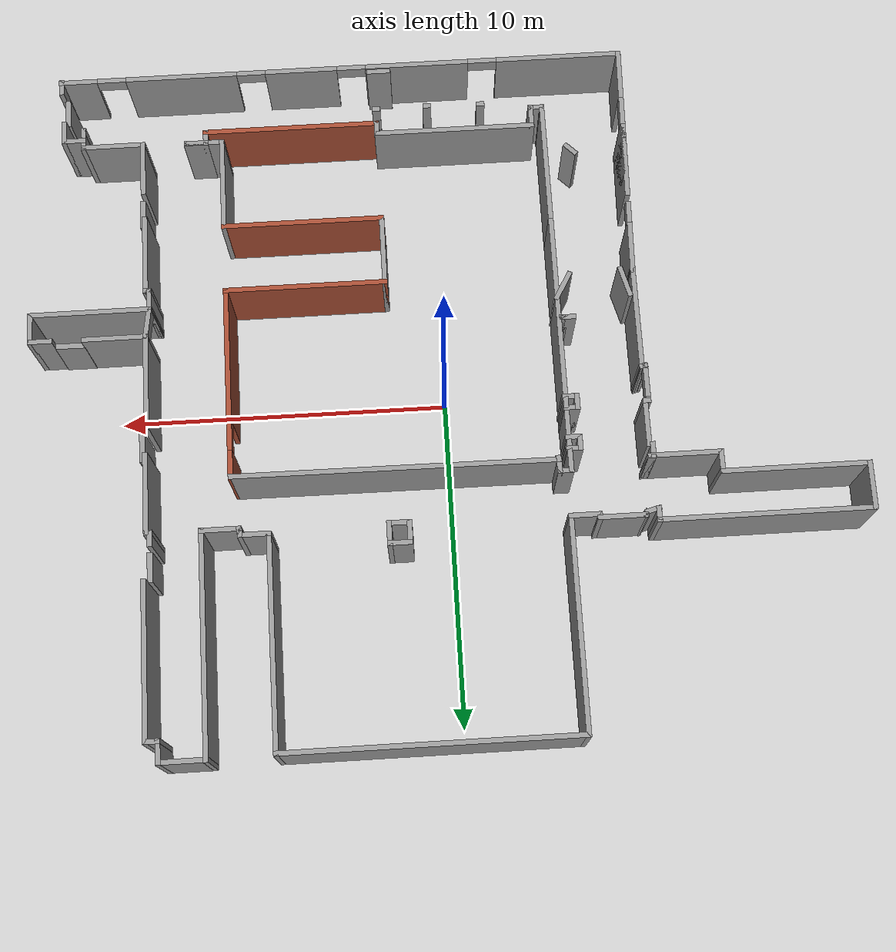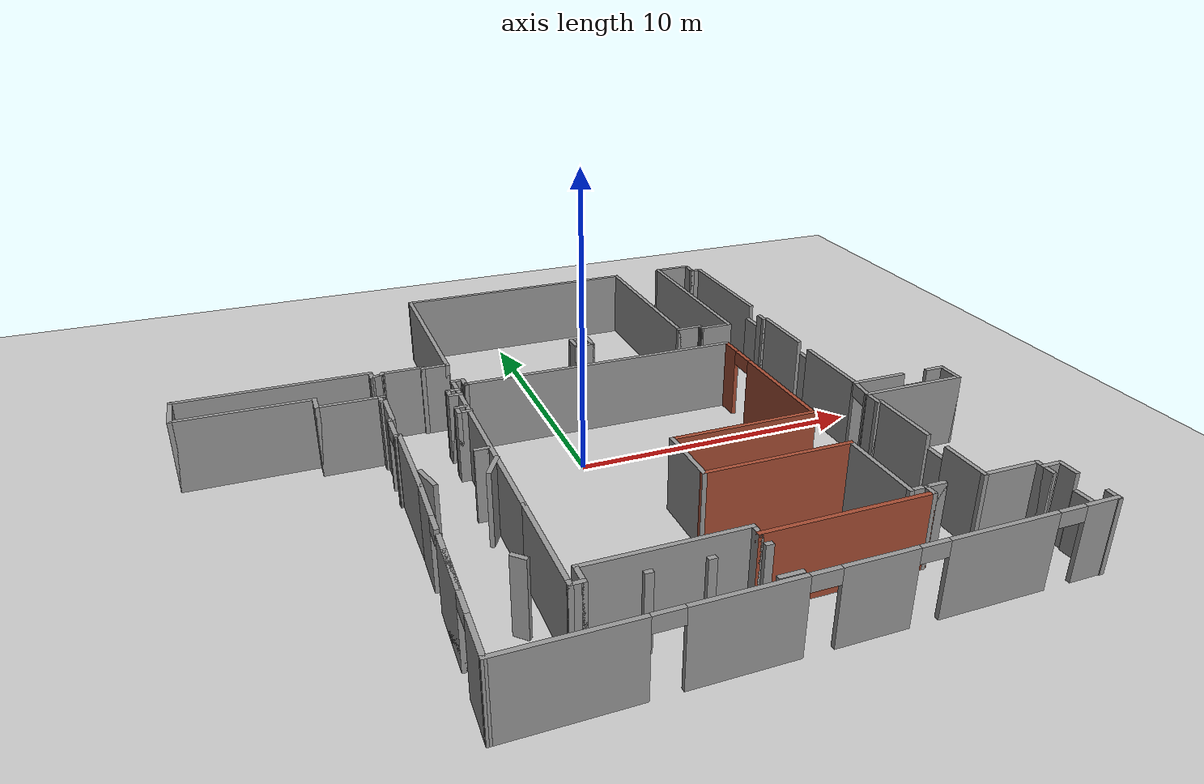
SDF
<?xml version="1.0" ?>
<sdf version="1.4">
  <world name="default">
    <include>
      <uri>model://ground_plane</uri>
    </include>
    <include>
      <uri>model://sun</uri>
    </include>
<model name="3rdFloor">
    <static>true</static>

<link name='Door_2'>
      <collision name='Door_2_Collision'>
        <geometry>
          <box>
            <size>0.9 0.17 2</size>
          </box>
        </geometry>
        <pose>0 0 1 0 -0 0</pose>
      </collision>
      <visual name='Door_2_Visual'>
        <pose>0 0 1 0 -0 0</pose>
        <geometry>
          <box>
            <size>0.9 0.17 2</size>
          </box>
        </geometry>
        <material>
          <script>
            <uri>file://media/materials/scripts/gazebo.material</uri>
            <name>Gazebo/Grey</name>
          </script>
        </material>
      </visual>
      <pose>11.3433 -9.80732 0 0 -0 1.5995</pose>
    </link>
    <link name='Door_3'>
      <collision name='Door_3_Collision'>
        <geometry>
          <box>
            <size>0.9 0.17 2</size>
          </box>
        </geometry>
        <pose>0 0 1 0 -0 0</pose>
      </collision>
      <visual name='Door_3_Visual'>
        <pose>0 0 1 0 -0 0</pose>
        <geometry>
          <box>
            <size>0.9 0.17 2</size>
          </box>
        </geometry>
        <material>
          <script>
            <uri>file://media/materials/scripts/gazebo.material</uri>
            <name>Gazebo/Grey</name>
          </script>
        </material>
      </visual>
      <pose>9.02 -6.21968 0 0 -0 1.5708</pose>
    </link>
    <link name='Door_4'>
      <collision name='Door_4_Collision'>
        <geometry>
          <box>
            <size>0.9 0.17 2</size>
          </box>
        </geometry>
        <pose>0 0 1 0 -0 0</pose>
      </collision>
      <visual name='Door_4_Visual'>
        <pose>0 0 1 0 -0 0</pose>
        <geometry>
          <box>
            <size>0.9 0.17 2</size>
          </box>
        </geometry>
        <material>
          <script>
            <uri>file://media/materials/scripts/gazebo.material</uri>
            <name>Gazebo/Grey</name>
          </script>
        </material>
      </visual>
      <pose>11.2709 -2.03728 0 0 -0 3.13685</pose>
    </link>
    <link name='Door_5'>
      <collision name='Door_5_Collision'>
        <geometry>
          <box>
            <size>0.9 0.17 2</size>
          </box>
        </geometry>
        <pose>0 0 1 0 -0 0</pose>
      </collision>
      <visual name='Door_5_Visual'>
        <pose>0 0 1 0 -0 0</pose>
        <geometry>
          <box>
            <size>0.9 0.17 2</size>
          </box>
        </geometry>
        <material>
          <script>
            <uri>file://media/materials/scripts/gazebo.material</uri>
            <name>Gazebo/Grey</name>
          </script>
        </material>
      </visual>
      <pose>9.12646 1.30865 0 0 -0 1.58598</pose>
    </link>
    <link name='Door_6'>
      <collision name='Door_6_Collision'>
        <geometry>
          <box>
            <size>0.9 0.17 2</size>
          </box>
        </geometry>
        <pose>0 0 1 0 -0 0</pose>
      </collision>
      <visual name='Door_6_Visual'>
        <pose>0 0 1 0 -0 0</pose>
        <geometry>
          <box>
            <size>0.9 0.17 2</size>
          </box>
        </geometry>
        <material>
          <script>
            <uri>file://media/materials/scripts/gazebo.material</uri>
            <name>Gazebo/Grey</name>
          </script>
        </material>
      </visual>
      <pose>8.94396 4.95875 0 0 -0 1.5708</pose>
    </link>
    <link name='Wall_0'>
      <pose>2.65717 -10.632 0 0 -0 0</pose>
      <visual name='Wall_0_Visual_0'>
        <pose>-6.9013 0 1.25 0 -0 0</pose>
        <geometry>
          <box>
            <size>3.94739 0.15 2.5</size>
          </box>
        </geometry>
        <material>
          <script>
            <uri>file://media/materials/scripts/gazebo.material</uri>
            <name>Gazebo/Grey</name>
          </script>
          <ambient>1 1 1 1</ambient>
        </material>
      </visual>
      <collision name='Wall_0_Collision_0'>
        <geometry>
          <box>
            <size>3.94739 0.15 2.5</size>
          </box>
        </geometry>
        <pose>-6.9013 0 1.25 0 -0 0</pose>
      </collision>
      <visual name='Wall_0_Visual_1'>
        <pose>-2.40206 0 1.25 0 -0 0</pose>
        <geometry>
          <box>
            <size>3.25109 0.15 2.5</size>
          </box>
        </geometry>
        <material>
          <script>
            <uri>file://media/materials/scripts/gazebo.material</uri>
            <name>Gazebo/Grey</name>
          </script>
          <ambient>1 1 1 1</ambient>
        </material>
      </visual>
      <collision name='Wall_0_Collision_1'>
        <geometry>
          <box>
            <size>3.25109 0.15 2.5</size>
          </box>
        </geometry>
        <pose>-2.40206 0 1.25 0 -0 0</pose>
      </collision>
      <visual name='Wall_0_Visual_2'>
        <pose>1.25653 0 1.25 0 -0 0</pose>
        <geometry>
          <box>
            <size>2.26609 0.15 2.5</size>
          </box>
        </geometry>
        <material>
          <script>
            <uri>file://media/materials/scripts/gazebo.material</uri>
            <name>Gazebo/Grey</name>
          </script>
          <ambient>1 1 1 1</ambient>
        </material>
      </visual>
      <collision name='Wall_0_Collision_2'>
        <geometry>
          <box>
            <size>2.26609 0.15 2.5</size>
          </box>
        </geometry>
        <pose>1.25653 0 1.25 0 -0 0</pose>
      </collision>
      <visual name='Wall_0_Visual_3'>
        <pose>5.03825 0 1.25 0 -0 0</pose>
        <geometry>
          <box>
            <size>3.49735 0.15 2.5</size>
          </box>
        </geometry>
        <material>
          <script>
            <uri>file://media/materials/scripts/gazebo.material</uri>
            <name>Gazebo/Grey</name>
          </script>
          <ambient>1 1 1 1</ambient>
        </material>
      </visual>
      <collision name='Wall_0_Collision_3'>
        <geometry>
          <box>
            <size>3.49735 0.15 2.5</size>
          </box>
        </geometry>
        <pose>5.03825 0 1.25 0 -0 0</pose>
      </collision>
      <visual name='Wall_0_Visual_4'>
        <pose>8.28096 0 1.25 0 -0 0</pose>
        <geometry>
          <box>
            <size>1.18808 0.15 2.5</size>
          </box>
        </geometry>
        <material>
          <script>
            <uri>file://media/materials/scripts/gazebo.material</uri>
            <name>Gazebo/Grey</name>
          </script>
          <ambient>1 1 1 1</ambient>
        </material>
      </visual>
      <collision name='Wall_0_Collision_4'>
        <geometry>
          <box>
            <size>1.18808 0.15 2.5</size>
          </box>
        </geometry>
        <pose>8.28096 0 1.25 0 -0 0</pose>
      </collision>
      <visual name='Wall_0_Visual_5'>
        <pose>-4.47761 0 2.25 0 -0 0</pose>
        <geometry>
          <box>
            <size>0.9 0.15 0.5</size>
          </box>
        </geometry>
        <material>
          <script>
            <uri>file://media/materials/scripts/gazebo.material</uri>
            <name>Gazebo/Grey</name>
          </script>
          <ambient>1 1 1 1</ambient>
        </material>
      </visual>
      <collision name='Wall_0_Collision_5'>
        <geometry>
          <box>
            <size>0.9 0.15 0.5</size>
          </box>
        </geometry>
        <pose>-4.47761 0 2.25 0 -0 0</pose>
      </collision>
      <visual name='Wall_0_Visual_6'>
        <pose>-0.326515 0 2.25 0 -0 0</pose>
        <geometry>
          <box>
            <size>0.9 0.15 0.5</size>
          </box>
        </geometry>
        <material>
          <script>
            <uri>file://media/materials/scripts/gazebo.material</uri>
            <name>Gazebo/Grey</name>
          </script>
          <ambient>1 1 1 1</ambient>
        </material>
      </visual>
      <collision name='Wall_0_Collision_6'>
        <geometry>
          <box>
            <size>0.9 0.15 0.5</size>
          </box>
        </geometry>
        <pose>-0.326515 0 2.25 0 -0 0</pose>
      </collision>
      <visual name='Wall_0_Visual_7'>
        <pose>2.83957 0 2.25 0 -0 0</pose>
        <geometry>
          <box>
            <size>0.9 0.15 0.5</size>
          </box>
        </geometry>
        <material>
          <script>
            <uri>file://media/materials/scripts/gazebo.material</uri>
            <name>Gazebo/Grey</name>
          </script>
          <ambient>1 1 1 1</ambient>
        </material>
      </visual>
      <collision name='Wall_0_Collision_7'>
        <geometry>
          <box>
            <size>0.9 0.15 0.5</size>
          </box>
        </geometry>
        <pose>2.83957 0 2.25 0 -0 0</pose>
      </collision>
      <visual name='Wall_0_Visual_8'>
        <pose>7.23692 0 2.25 0 -0 0</pose>
        <geometry>
          <box>
            <size>0.9 0.15 0.5</size>
          </box>
        </geometry>
        <material>
          <script>
            <uri>file://media/materials/scripts/gazebo.material</uri>
            <name>Gazebo/Grey</name>
          </script>
          <ambient>1 1 1 1</ambient>
        </material>
      </visual>
      <collision name='Wall_0_Collision_8'>
        <geometry>
          <box>
            <size>0.9 0.15 0.5</size>
          </box>
        </geometry>
        <pose>7.23692 0 2.25 0 -0 0</pose>
      </collision>
    </link>
    <link name='Wall_10'>
      <collision name='Wall_10_Collision'>
        <geometry>
          <box>
            <size>0.75 0.15 2.5</size>
          </box>
        </geometry>
        <pose>0 0 1.25 0 -0 0</pose>
      </collision>
      <visual name='Wall_10_Visual'>
        <pose>0 0 1.25 0 -0 0</pose>
        <geometry>
          <box>
            <size>0.75 0.15 2.5</size>
          </box>
        </geometry>
        <material>
          <script>
            <uri>file://media/materials/scripts/gazebo.material</uri>
            <name>Gazebo/Grey</name>
          </script>
          <ambient>1 1 1 1</ambient>
        </material>
      </visual>
      <pose>11.3774 -8.91581 0 0 -0 1.5708</pose>
    </link>
    <link name='Wall_101'>
      <collision name='Wall_101_Collision'>
        <geometry>
          <box>
            <size>0.25 0.15 2.5</size>
          </box>
        </geometry>
        <pose>0 0 1.25 0 -0 0</pose>
      </collision>
      <visual name='Wall_101_Visual'>
        <pose>0 0 1.25 0 -0 0</pose>
        <geometry>
          <box>
            <size>0.25 0.15 2.5</size>
          </box>
        </geometry>
        <material>
          <script>
            <uri>file://media/materials/scripts/gazebo.material</uri>
            <name>Gazebo/Grey</name>
          </script>
          <ambient>1 1 1 1</ambient>
        </material>
      </visual>
      <pose>-3.72513 -1.89943 0 0 -0 0</pose>
    </link>
    <link name='Wall_102'>
      <collision name='Wall_102_Collision'>
        <geometry>
          <box>
            <size>0.25 0.15 2.5</size>
          </box>
        </geometry>
        <pose>0 0 1.25 0 -0 0</pose>
      </collision>
      <visual name='Wall_102_Visual'>
        <pose>0 0 1.25 0 -0 0</pose>
        <geometry>
          <box>
            <size>0.25 0.15 2.5</size>
          </box>
        </geometry>
        <material>
          <script>
            <uri>file://media/materials/scripts/gazebo.material</uri>
            <name>Gazebo/Grey</name>
          </script>
          <ambient>1 1 1 1</ambient>
        </material>
      </visual>
      <pose>-3.72513 -1.89943 0 0 -0 3.14159</pose>
    </link>
    <link name='Wall_104'>
      <collision name='Wall_104_Collision'>
        <geometry>
          <box>
            <size>0.5 0.15 2.5</size>
          </box>
        </geometry>
        <pose>0 0 1.25 0 -0 0</pose>
      </collision>
      <visual name='Wall_104_Visual'>
        <pose>0 0 1.25 0 -0 0</pose>
        <geometry>
          <box>
            <size>0.5 0.15 2.5</size>
          </box>
        </geometry>
        <material>
          <script>
            <uri>file://media/materials/scripts/gazebo.material</uri>
            <name>Gazebo/Grey</name>
          </script>
          <ambient>1 1 1 1</ambient>
        </material>
      </visual>
      <pose>-3.85013 -1.89943 0 0 -0 3.14159</pose>
    </link>
    <link name='Wall_106'>
      <collision name='Wall_106_Collision'>
        <geometry>
          <box>
            <size>0.5 0.15 2.5</size>
          </box>
        </geometry>
        <pose>0 0 1.25 0 -0 0</pose>
      </collision>
      <visual name='Wall_106_Visual'>
        <pose>0 0 1.25 0 -0 0</pose>
        <geometry>
          <box>
            <size>0.5 0.15 2.5</size>
          </box>
        </geometry>
        <material>
          <script>
            <uri>file://media/materials/scripts/gazebo.material</uri>
            <name>Gazebo/Grey</name>
          </script>
          <ambient>1 1 1 1</ambient>
        </material>
      </visual>
      <pose>-3.73223 2.2205 0 0 -0 3.14159</pose>
    </link>
    <link name='Wall_107'>
      <collision name='Wall_107_Collision'>
        <geometry>
          <box>
            <size>0.5 0.15 2.5</size>
          </box>
        </geometry>
        <pose>0 0 1.25 0 -0 0</pose>
      </collision>
      <visual name='Wall_107_Visual'>
        <pose>0 0 1.25 0 -0 0</pose>
        <geometry>
          <box>
            <size>0.5 0.15 2.5</size>
          </box>
        </geometry>
        <material>
          <script>
            <uri>file://media/materials/scripts/gazebo.material</uri>
            <name>Gazebo/Grey</name>
          </script>
          <ambient>1 1 1 1</ambient>
        </material>
      </visual>
      <pose>-3.90723 2.0455 0 0 0 -1.5708</pose>
    </link>
    <link name='Wall_108'>
      <collision name='Wall_108_Collision'>
        <geometry>
          <box>
            <size>0.5 0.15 2.5</size>
          </box>
        </geometry>
        <pose>0 0 1.25 0 -0 0</pose>
      </collision>
      <visual name='Wall_108_Visual'>
        <pose>0 0 1.25 0 -0 0</pose>
        <geometry>
          <box>
            <size>0.5 0.15 2.5</size>
          </box>
        </geometry>
        <material>
          <script>
            <uri>file://media/materials/scripts/gazebo.material</uri>
            <name>Gazebo/Grey</name>
          </script>
          <ambient>1 1 1 1</ambient>
        </material>
      </visual>
      <pose>-3.73223 1.8705 0 0 -0 0</pose>
    </link>
    <link name='Wall_11'>
      <collision name='Wall_11_Collision'>
        <geometry>
          <box>
            <size>0.75 0.15 2.5</size>
          </box>
        </geometry>
        <pose>0 0 1.25 0 -0 0</pose>
      </collision>
      <visual name='Wall_11_Visual'>
        <pose>0 0 1.25 0 -0 0</pose>
        <geometry>
          <box>
            <size>0.75 0.15 2.5</size>
          </box>
        </geometry>
        <material>
          <script>
            <uri>file://media/materials/scripts/gazebo.material</uri>
            <name>Gazebo/Grey</name>
          </script>
          <ambient>1 1 1 1</ambient>
        </material>
      </visual>
      <pose>11.0774 -8.61581 0 0 -0 3.14159</pose>
    </link>
    <link name='Wall_110'>
      <collision name='Wall_110_Collision'>
        <geometry>
          <box>
            <size>0.5 0.15 2.5</size>
          </box>
        </geometry>
        <pose>0 0 1.25 0 -0 0</pose>
      </collision>
      <visual name='Wall_110_Visual'>
        <pose>0 0 1.25 0 -0 0</pose>
        <geometry>
          <box>
            <size>0.5 0.15 2.5</size>
          </box>
        </geometry>
        <material>
          <script>
            <uri>file://media/materials/scripts/gazebo.material</uri>
            <name>Gazebo/Grey</name>
          </script>
          <ambient>1 1 1 1</ambient>
        </material>
      </visual>
      <pose>-3.74744 0.958175 0 0 -0 3.14159</pose>
    </link>
    <link name='Wall_111'>
      <collision name='Wall_111_Collision'>
        <geometry>
          <box>
            <size>0.5 0.15 2.5</size>
          </box>
        </geometry>
        <pose>0 0 1.25 0 -0 0</pose>
      </collision>
      <visual name='Wall_111_Visual'>
        <pose>0 0 1.25 0 -0 0</pose>
        <geometry>
          <box>
            <size>0.5 0.15 2.5</size>
          </box>
        </geometry>
        <material>
          <script>
            <uri>file://media/materials/scripts/gazebo.material</uri>
            <name>Gazebo/Grey</name>
          </script>
          <ambient>1 1 1 1</ambient>
        </material>
      </visual>
      <pose>-3.92244 0.783175 0 0 0 -1.5708</pose>
    </link>
    <link name='Wall_112'>
      <collision name='Wall_112_Collision'>
        <geometry>
          <box>
            <size>0.515209 0.15 2.5</size>
          </box>
        </geometry>
        <pose>0 0 1.25 0 -0 0</pose>
      </collision>
      <visual name='Wall_112_Visual'>
        <pose>0 0 1.25 0 -0 0</pose>
        <geometry>
          <box>
            <size>0.515209 0.15 2.5</size>
          </box>
        </geometry>
        <material>
          <script>
            <uri>file://media/materials/scripts/gazebo.material</uri>
            <name>Gazebo/Grey</name>
          </script>
          <ambient>1 1 1 1</ambient>
        </material>
      </visual>
      <pose>-3.73983 0.608175 0 0 -0 0</pose>
    </link>
    <link name='Wall_114'>
      <collision name='Wall_114_Collision'>
        <geometry>
          <box>
            <size>0.25 0.15 2.5</size>
          </box>
        </geometry>
        <pose>0 0 1.25 0 -0 0</pose>
      </collision>
      <visual name='Wall_114_Visual'>
        <pose>0 0 1.25 0 -0 0</pose>
        <geometry>
          <box>
            <size>0.25 0.15 2.5</size>
          </box>
        </geometry>
        <material>
          <script>
            <uri>file://media/materials/scripts/gazebo.material</uri>
            <name>Gazebo/Grey</name>
          </script>
          <ambient>1 1 1 1</ambient>
        </material>
      </visual>
      <pose>-1.66801 -9.13362 0 0 -0 0</pose>
    </link>
    <link name='Wall_116'>
      <collision name='Wall_116_Collision'>
        <geometry>
          <box>
            <size>0.25 0.15 2.5</size>
          </box>
        </geometry>
        <pose>0 0 1.25 0 -0 0</pose>
      </collision>
      <visual name='Wall_116_Visual'>
        <pose>0 0 1.25 0 -0 0</pose>
        <geometry>
          <box>
            <size>0.25 0.15 2.5</size>
          </box>
        </geometry>
        <material>
          <script>
            <uri>file://media/materials/scripts/gazebo.material</uri>
            <name>Gazebo/Grey</name>
          </script>
          <ambient>1 1 1 1</ambient>
        </material>
      </visual>
      <pose>0.011032 -9.1686 0 0 -0 0</pose>
    </link>
    <link name='Wall_118'>
      <collision name='Wall_118_Collision'>
        <geometry>
          <box>
            <size>0.25 0.15 2.5</size>
          </box>
        </geometry>
        <pose>0 0 1.25 0 -0 0</pose>
      </collision>
      <visual name='Wall_118_Visual'>
        <pose>0 0 1.25 0 -0 0</pose>
        <geometry>
          <box>
            <size>0.25 0.15 2.5</size>
          </box>
        </geometry>
        <material>
          <script>
            <uri>file://media/materials/scripts/gazebo.material</uri>
            <name>Gazebo/Grey</name>
          </script>
          <ambient>1 1 1 1</ambient>
        </material>
      </visual>
      <pose>1.60263 -9.15111 0 0 -0 0</pose>
    </link>
    <link name='Wall_12'>
      <collision name='Wall_12_Collision'>
        <geometry>
          <box>
            <size>0.5 0.15 2.5</size>
          </box>
        </geometry>
        <pose>0 0 1.25 0 -0 0</pose>
      </collision>
      <visual name='Wall_12_Visual'>
        <pose>0 0 1.25 0 -0 0</pose>
        <geometry>
          <box>
            <size>0.5 0.15 2.5</size>
          </box>
        </geometry>
        <material>
          <script>
            <uri>file://media/materials/scripts/gazebo.material</uri>
            <name>Gazebo/Grey</name>
          </script>
          <ambient>1 1 1 1</ambient>
        </material>
      </visual>
      <pose>10.7774 -8.79081 0 0 0 -1.5708</pose>
    </link>
    <link name='Wall_120'>
      <collision name='Wall_120_Collision'>
        <geometry>
          <box>
            <size>0.5 0.15 2.5</size>
          </box>
        </geometry>
        <pose>0 0 1.25 0 -0 0</pose>
      </collision>
      <visual name='Wall_120_Visual'>
        <pose>0 0 1.25 0 -0 0</pose>
        <geometry>
          <box>
            <size>0.5 0.15 2.5</size>
          </box>
        </geometry>
        <material>
          <script>
            <uri>file://media/materials/scripts/gazebo.material</uri>
            <name>Gazebo/Grey</name>
          </script>
          <ambient>1 1 1 1</ambient>
        </material>
      </visual>
      <pose>-4.37519 -7.42091 0 0 0 -0.785398</pose>
    </link>
    <link name='Wall_122'>
      <collision name='Wall_122_Collision'>
        <geometry>
          <box>
            <size>1 0.15 2.5</size>
          </box>
        </geometry>
        <pose>0 0 1.25 0 -0 0</pose>
      </collision>
      <visual name='Wall_122_Visual'>
        <pose>0 0 1.25 0 -0 0</pose>
        <geometry>
          <box>
            <size>1 0.15 2.5</size>
          </box>
        </geometry>
        <material>
          <script>
            <uri>file://media/materials/scripts/gazebo.material</uri>
            <name>Gazebo/Grey</name>
          </script>
          <ambient>1 1 1 1</ambient>
        </material>
      </visual>
      <pose>-5.6895 -2.93592 0 0 0 -1.309</pose>
    </link>
    <link name='Wall_124'>
      <collision name='Wall_124_Collision'>
        <geometry>
          <box>
            <size>1 0.15 2.5</size>
          </box>
        </geometry>
        <pose>0 0 1.25 0 -0 0</pose>
      </collision>
      <visual name='Wall_124_Visual'>
        <pose>0 0 1.25 0 -0 0</pose>
        <geometry>
          <box>
            <size>1 0.15 2.5</size>
          </box>
        </geometry>
        <material>
          <script>
            <uri>file://media/materials/scripts/gazebo.material</uri>
            <name>Gazebo/Grey</name>
          </script>
          <ambient>1 1 1 1</ambient>
        </material>
      </visual>
      <pose>-3.79076 -2.91095 0 0 0 -2.0944</pose>
    </link>
    <link name='Wall_126'>
      <collision name='Wall_126_Collision'>
        <geometry>
          <box>
            <size>0.75 0.15 2.5</size>
          </box>
        </geometry>
        <pose>0 0 1.25 0 -0 0</pose>
      </collision>
      <visual name='Wall_126_Visual'>
        <pose>0 0 1.25 0 -0 0</pose>
        <geometry>
          <box>
            <size>0.75 0.15 2.5</size>
          </box>
        </geometry>
        <material>
          <script>
            <uri>file://media/materials/scripts/gazebo.material</uri>
            <name>Gazebo/Grey</name>
          </script>
          <ambient>1 1 1 1</ambient>
        </material>
      </visual>
      <pose>1.46976 -10.4503 0 0 -0 0</pose>
    </link>
    <link name='Wall_128'>
      <pose>8.85867 -2.47097 0 0 0 -1.70903</pose>
      <visual name='Wall_128_Visual_0'>
        <pose>-0.493314 0 1.25 0 -0 0</pose>
        <geometry>
          <box>
            <size>0.039123 0.15 2.5</size>
          </box>
        </geometry>
        <material>
          <script>
            <uri>file://media/materials/scripts/gazebo.material</uri>
            <name>Gazebo/Grey</name>
          </script>
          <ambient>1 1 1 1</ambient>
        </material>
      </visual>
      <collision name='Wall_128_Collision_0'>
        <geometry>
          <box>
            <size>0.039123 0.15 2.5</size>
          </box>
        </geometry>
        <pose>-0.493314 0 1.25 0 -0 0</pose>
      </collision>
      <visual name='Wall_128_Visual_1'>
        <pose>0.469562 0 1.25 0 -0 0</pose>
        <geometry>
          <box>
            <size>0.086627 0.15 2.5</size>
          </box>
        </geometry>
        <material>
          <script>
            <uri>file://media/materials/scripts/gazebo.material</uri>
            <name>Gazebo/Grey</name>
          </script>
          <ambient>1 1 1 1</ambient>
        </material>
      </visual>
      <collision name='Wall_128_Collision_1'>
        <geometry>
          <box>
            <size>0.086627 0.15 2.5</size>
          </box>
        </geometry>
        <pose>0.469562 0 1.25 0 -0 0</pose>
      </collision>
      <visual name='Wall_128_Visual_2'>
        <pose>-0.023752 0 2.25 0 -0 0</pose>
        <geometry>
          <box>
            <size>0.9 0.15 0.5</size>
          </box>
        </geometry>
        <material>
          <script>
            <uri>file://media/materials/scripts/gazebo.material</uri>
            <name>Gazebo/Grey</name>
          </script>
          <ambient>1 1 1 1</ambient>
        </material>
      </visual>
      <collision name='Wall_128_Collision_2'>
        <geometry>
          <box>
            <size>0.9 0.15 0.5</size>
          </box>
        </geometry>
        <pose>-0.023752 0 2.25 0 -0 0</pose>
      </collision>
    </link>
    <link name='Wall_13'>
      <collision name='Wall_13_Collision'>
        <geometry>
          <box>
            <size>0.75 0.15 2.5</size>
          </box>
        </geometry>
        <pose>0 0 1.25 0 -0 0</pose>
      </collision>
      <visual name='Wall_13_Visual'>
        <pose>0 0 1.25 0 -0 0</pose>
        <geometry>
          <box>
            <size>0.75 0.15 2.5</size>
          </box>
        </geometry>
        <material>
          <script>
            <uri>file://media/materials/scripts/gazebo.material</uri>
            <name>Gazebo/Grey</name>
          </script>
          <ambient>1 1 1 1</ambient>
        </material>
      </visual>
      <pose>10.7774 -8.66581 0 0 -0 1.5708</pose>
    </link>
    <link name='Wall_14'>
      <collision name='Wall_14_Collision'>
        <geometry>
          <box>
            <size>2 0.15 2.5</size>
          </box>
        </geometry>
        <pose>0 0 1.25 0 -0 0</pose>
      </collision>
      <visual name='Wall_14_Visual'>
        <pose>0 0 1.25 0 -0 0</pose>
        <geometry>
          <box>
            <size>2 0.15 2.5</size>
          </box>
        </geometry>
        <material>
          <script>
            <uri>file://media/materials/scripts/gazebo.material</uri>
            <name>Gazebo/Grey</name>
          </script>
          <ambient>1 1 1 1</ambient>
        </material>
      </visual>
      <pose>9.85236 -8.36581 0 0 -0 3.14159</pose>
    </link>
    <link name='Wall_15'>
      <collision name='Wall_15_Collision'>
        <geometry>
          <box>
            <size>1.75 0.15 2.5</size>
          </box>
        </geometry>
        <pose>0 0 1.25 0 -0 0</pose>
      </collision>
      <visual name='Wall_15_Visual'>
        <pose>0 0 1.25 0 -0 0</pose>
        <geometry>
          <box>
            <size>1.75 0.15 2.5</size>
          </box>
        </geometry>
        <material>
          <script>
            <uri>file://media/materials/scripts/gazebo.material</uri>
            <name>Gazebo/Grey</name>
          </script>
          <ambient>1 1 1 1</ambient>
        </material>
      </visual>
      <pose>8.92736 -7.56581 0 0 -0 1.5708</pose>
    </link>
    <link name='Wall_17'>
      <collision name='Wall_17_Collision'>
        <geometry>
          <box>
            <size>2.5 0.15 2.5</size>
          </box>
        </geometry>
        <pose>0 0 1.25 0 -0 0</pose>
      </collision>
      <visual name='Wall_17_Visual'>
        <pose>0 0 1.25 0 -0 0</pose>
        <geometry>
          <box>
            <size>2.5 0.15 2.5</size>
          </box>
        </geometry>
        <material>
          <script>
            <uri>file://media/materials/scripts/gazebo.material</uri>
            <name>Gazebo/Grey</name>
          </script>
          <ambient>1 1 1 1</ambient>
        </material>
      </visual>
      <pose>8.89833 -4.67967 0 0 -0 1.5708</pose>
    </link>
    <link name='Wall_18'>
      <collision name='Wall_18_Collision'>
        <geometry>
          <box>
            <size>0.25 0.15 2.5</size>
          </box>
        </geometry>
        <pose>0 0 1.25 0 -0 0</pose>
      </collision>
      <visual name='Wall_18_Visual'>
        <pose>0 0 1.25 0 -0 0</pose>
        <geometry>
          <box>
            <size>0.25 0.15 2.5</size>
          </box>
        </geometry>
        <material>
          <script>
            <uri>file://media/materials/scripts/gazebo.material</uri>
            <name>Gazebo/Grey</name>
          </script>
          <ambient>1 1 1 1</ambient>
        </material>
      </visual>
      <pose>8.84833 -3.50467 0 0 -0 3.14159</pose>
    </link>
    <link name='Wall_19'>
      <collision name='Wall_19_Collision'>
        <geometry>
          <box>
            <size>0.75 0.15 2.5</size>
          </box>
        </geometry>
        <pose>0 0 1.25 0 -0 0</pose>
      </collision>
      <visual name='Wall_19_Visual'>
        <pose>0 0 1.25 0 -0 0</pose>
        <geometry>
          <box>
            <size>0.75 0.15 2.5</size>
          </box>
        </geometry>
        <material>
          <script>
            <uri>file://media/materials/scripts/gazebo.material</uri>
            <name>Gazebo/Grey</name>
          </script>
          <ambient>1 1 1 1</ambient>
        </material>
      </visual>
      <pose>8.79833 -3.20467 0 0 -0 1.5708</pose>
    </link>
    <link name='Wall_20'>
      <collision name='Wall_20_Collision'>
        <geometry>
          <box>
            <size>3.75 0.15 2.5</size>
          </box>
        </geometry>
        <pose>0 0 1.25 0 -0 0</pose>
      </collision>
      <visual name='Wall_20_Visual'>
        <pose>0 0 1.25 0 -0 0</pose>
        <geometry>
          <box>
            <size>3.75 0.15 2.5</size>
          </box>
        </geometry>
        <material>
          <script>
            <uri>file://media/materials/scripts/gazebo.material</uri>
            <name>Gazebo/Grey</name>
          </script>
          <ambient>1 1 1 1</ambient>
        </material>
      </visual>
      <pose>10.5983 -2.90467 0 0 -0 0</pose>
    </link>
    <link name='Wall_21'>
      <collision name='Wall_21_Collision'>
        <geometry>
          <box>
            <size>1 0.15 2.5</size>
          </box>
        </geometry>
        <pose>0 0 1.25 0 -0 0</pose>
      </collision>
      <visual name='Wall_21_Visual'>
        <pose>0 0 1.25 0 -0 0</pose>
        <geometry>
          <box>
            <size>1 0.15 2.5</size>
          </box>
        </geometry>
        <material>
          <script>
            <uri>file://media/materials/scripts/gazebo.material</uri>
            <name>Gazebo/Grey</name>
          </script>
          <ambient>1 1 1 1</ambient>
        </material>
      </visual>
      <pose>12.3983 -2.47967 0 0 -0 1.5708</pose>
    </link>
    <link name='Wall_22'>
      <collision name='Wall_22_Collision'>
        <geometry>
          <box>
            <size>0.75 0.15 2.5</size>
          </box>
        </geometry>
        <pose>0 0 1.25 0 -0 0</pose>
      </collision>
      <visual name='Wall_22_Visual'>
        <pose>0 0 1.25 0 -0 0</pose>
        <geometry>
          <box>
            <size>0.75 0.15 2.5</size>
          </box>
        </geometry>
        <material>
          <script>
            <uri>file://media/materials/scripts/gazebo.material</uri>
            <name>Gazebo/Grey</name>
          </script>
          <ambient>1 1 1 1</ambient>
        </material>
      </visual>
      <pose>12.0983 -2.05467 0 0 -0 3.14159</pose>
    </link>
    <link name='Wall_24'>
      <collision name='Wall_24_Collision'>
        <geometry>
          <box>
            <size>2 0.15 2.5</size>
          </box>
        </geometry>
        <pose>0 0 1.25 0 -0 0</pose>
      </collision>
      <visual name='Wall_24_Visual'>
        <pose>0 0 1.25 0 -0 0</pose>
        <geometry>
          <box>
            <size>2 0.15 2.5</size>
          </box>
        </geometry>
        <material>
          <script>
            <uri>file://media/materials/scripts/gazebo.material</uri>
            <name>Gazebo/Grey</name>
          </script>
          <ambient>1 1 1 1</ambient>
        </material>
      </visual>
      <pose>9.84401 -2.03728 0 0 -0 3.14159</pose>
    </link>
    <link name='Wall_27'>
      <collision name='Wall_27_Collision'>
        <geometry>
          <box>
            <size>3 0.15 2.5</size>
          </box>
        </geometry>
        <pose>0 0 1.25 0 -0 0</pose>
      </collision>
      <visual name='Wall_27_Visual'>
        <pose>0 0 1.25 0 -0 0</pose>
        <geometry>
          <box>
            <size>3 0.15 2.5</size>
          </box>
        </geometry>
        <material>
          <script>
            <uri>file://media/materials/scripts/gazebo.material</uri>
            <name>Gazebo/Grey</name>
          </script>
          <ambient>1 1 1 1</ambient>
        </material>
      </visual>
      <pose>8.91901 -0.612276 0 0 -0 1.5708</pose>
    </link>
    <link name='Wall_29'>
      <collision name='Wall_29_Collision'>
        <geometry>
          <box>
            <size>2.5 0.15 2.5</size>
          </box>
        </geometry>
        <pose>0 0 1.25 0 -0 0</pose>
      </collision>
      <visual name='Wall_29_Visual'>
        <pose>0 0 1.25 0 -0 0</pose>
        <geometry>
          <box>
            <size>2.5 0.15 2.5</size>
          </box>
        </geometry>
        <material>
          <script>
            <uri>file://media/materials/scripts/gazebo.material</uri>
            <name>Gazebo/Grey</name>
          </script>
          <ambient>1 1 1 1</ambient>
        </material>
      </visual>
      <pose>8.97437 2.84866 0 0 -0 1.5708</pose>
    </link>
    <link name='Wall_31'>
      <collision name='Wall_31_Collision'>
        <geometry>
          <box>
            <size>0.25 0.15 2.5</size>
          </box>
        </geometry>
        <pose>0 0 1.25 0 -0 0</pose>
      </collision>
      <visual name='Wall_31_Visual'>
        <pose>0 0 1.25 0 -0 0</pose>
        <geometry>
          <box>
            <size>0.25 0.15 2.5</size>
          </box>
        </geometry>
        <material>
          <script>
            <uri>file://media/materials/scripts/gazebo.material</uri>
            <name>Gazebo/Grey</name>
          </script>
          <ambient>1 1 1 1</ambient>
        </material>
      </visual>
      <pose>8.92437 4.02366 0 0 -0 3.14159</pose>
    </link>
    <link name='Wall_32'>
      <collision name='Wall_32_Collision'>
        <geometry>
          <box>
            <size>0.5 0.15 2.5</size>
          </box>
        </geometry>
        <pose>0 0 1.25 0 -0 0</pose>
      </collision>
      <visual name='Wall_32_Visual'>
        <pose>0 0 1.25 0 -0 0</pose>
        <geometry>
          <box>
            <size>0.5 0.15 2.5</size>
          </box>
        </geometry>
        <material>
          <script>
            <uri>file://media/materials/scripts/gazebo.material</uri>
            <name>Gazebo/Grey</name>
          </script>
          <ambient>1 1 1 1</ambient>
        </material>
      </visual>
      <pose>8.87437 4.19866 0 0 -0 1.5708</pose>
    </link>
    <link name='Wall_34'>
      <collision name='Wall_34_Collision'>
        <geometry>
          <box>
            <size>4.75 0.15 2.5</size>
          </box>
        </geometry>
        <pose>0 0 1.25 0 -0 0</pose>
      </collision>
      <visual name='Wall_34_Visual'>
        <pose>0 0 1.25 0 -0 0</pose>
        <geometry>
          <box>
            <size>4.75 0.15 2.5</size>
          </box>
        </geometry>
        <material>
          <script>
            <uri>file://media/materials/scripts/gazebo.material</uri>
            <name>Gazebo/Grey</name>
          </script>
          <ambient>1 1 1 1</ambient>
        </material>
      </visual>
      <pose>9.06563 7.76064 0 0 -0 1.5708</pose>
    </link>
    <link name='Wall_35'>
      <collision name='Wall_35_Collision'>
        <geometry>
          <box>
            <size>0.5 0.15 2.5</size>
          </box>
        </geometry>
        <pose>0 0 1.25 0 -0 0</pose>
      </collision>
      <visual name='Wall_35_Visual'>
        <pose>0 0 1.25 0 -0 0</pose>
        <geometry>
          <box>
            <size>0.5 0.15 2.5</size>
          </box>
        </geometry>
        <material>
          <script>
            <uri>file://media/materials/scripts/gazebo.material</uri>
            <name>Gazebo/Grey</name>
          </script>
          <ambient>1 1 1 1</ambient>
        </material>
      </visual>
      <pose>8.89063 10.0606 0 0 -0 3.14159</pose>
    </link>
    <link name='Wall_36'>
      <collision name='Wall_36_Collision'>
        <geometry>
          <box>
            <size>0.75 0.15 2.5</size>
          </box>
        </geometry>
        <pose>0 0 1.25 0 -0 0</pose>
      </collision>
      <visual name='Wall_36_Visual'>
        <pose>0 0 1.25 0 -0 0</pose>
        <geometry>
          <box>
            <size>0.75 0.15 2.5</size>
          </box>
        </geometry>
        <material>
          <script>
            <uri>file://media/materials/scripts/gazebo.material</uri>
            <name>Gazebo/Grey</name>
          </script>
          <ambient>1 1 1 1</ambient>
        </material>
      </visual>
      <pose>8.71563 10.3606 0 0 -0 1.5708</pose>
    </link>
    <link name='Wall_37'>
      <collision name='Wall_37_Collision'>
        <geometry>
          <box>
            <size>1.5 0.15 2.5</size>
          </box>
        </geometry>
        <pose>0 0 1.25 0 -0 0</pose>
      </collision>
      <visual name='Wall_37_Visual'>
        <pose>0 0 1.25 0 -0 0</pose>
        <geometry>
          <box>
            <size>1.5 0.15 2.5</size>
          </box>
        </geometry>
        <material>
          <script>
            <uri>file://media/materials/scripts/gazebo.material</uri>
            <name>Gazebo/Grey</name>
          </script>
          <ambient>1 1 1 1</ambient>
        </material>
      </visual>
      <pose>8.04063 10.6606 0 0 -0 3.14159</pose>
    </link>
    <link name='Wall_38'>
      <collision name='Wall_38_Collision'>
        <geometry>
          <box>
            <size>6.75 0.15 2.5</size>
          </box>
        </geometry>
        <pose>0 0 1.25 0 -0 0</pose>
      </collision>
      <visual name='Wall_38_Visual'>
        <pose>0 0 1.25 0 -0 0</pose>
        <geometry>
          <box>
            <size>6.75 0.15 2.5</size>
          </box>
        </geometry>
        <material>
          <script>
            <uri>file://media/materials/scripts/gazebo.material</uri>
            <name>Gazebo/Grey</name>
          </script>
          <ambient>1 1 1 1</ambient>
        </material>
      </visual>
      <pose>7.36563 7.36064 0 0 0 -1.5708</pose>
    </link>
    <link name='Wall_39'>
      <collision name='Wall_39_Collision'>
        <geometry>
          <box>
            <size>1.25 0.15 2.5</size>
          </box>
        </geometry>
        <pose>0 0 1.25 0 -0 0</pose>
      </collision>
      <visual name='Wall_39_Visual'>
        <pose>0 0 1.25 0 -0 0</pose>
        <geometry>
          <box>
            <size>1.25 0.15 2.5</size>
          </box>
        </geometry>
        <material>
          <script>
            <uri>file://media/materials/scripts/gazebo.material</uri>
            <name>Gazebo/Grey</name>
          </script>
          <ambient>1 1 1 1</ambient>
        </material>
      </visual>
      <pose>6.81563 4.06064 0 0 -0 3.14159</pose>
    </link>
    <link name='Wall_40'>
      <collision name='Wall_40_Collision'>
        <geometry>
          <box>
            <size>0.25 0.15 2.5</size>
          </box>
        </geometry>
        <pose>0 0 1.25 0 -0 0</pose>
      </collision>
      <visual name='Wall_40_Visual'>
        <pose>0 0 1.25 0 -0 0</pose>
        <geometry>
          <box>
            <size>0.25 0.15 2.5</size>
          </box>
        </geometry>
        <material>
          <script>
            <uri>file://media/materials/scripts/gazebo.material</uri>
            <name>Gazebo/Grey</name>
          </script>
          <ambient>1 1 1 1</ambient>
        </material>
      </visual>
      <pose>6.25269 4.10893 0 0 -0 1.8326</pose>
    </link>
    <link name='Wall_41'>
      <collision name='Wall_41_Collision'>
        <geometry>
          <box>
            <size>0.25 0.15 2.5</size>
          </box>
        </geometry>
        <pose>0 0 1.25 0 -0 0</pose>
      </collision>
      <visual name='Wall_41_Visual'>
        <pose>0 0 1.25 0 -0 0</pose>
        <geometry>
          <box>
            <size>0.25 0.15 2.5</size>
          </box>
        </geometry>
        <material>
          <script>
            <uri>file://media/materials/scripts/gazebo.material</uri>
            <name>Gazebo/Grey</name>
          </script>
          <ambient>1 1 1 1</ambient>
        </material>
      </visual>
      <pose>6.23975 4.20723 0 0 -0 1.5708</pose>
    </link>
    <link name='Wall_42'>
      <collision name='Wall_42_Collision'>
        <geometry>
          <box>
            <size>1 0.15 2.5</size>
          </box>
        </geometry>
        <pose>0 0 1.25 0 -0 0</pose>
      </collision>
      <visual name='Wall_42_Visual'>
        <pose>0 0 1.25 0 -0 0</pose>
        <geometry>
          <box>
            <size>1 0.15 2.5</size>
          </box>
        </geometry>
        <material>
          <script>
            <uri>file://media/materials/scripts/gazebo.material</uri>
            <name>Gazebo/Grey</name>
          </script>
          <ambient>1 1 1 1</ambient>
        </material>
      </visual>
      <pose>5.81474 4.25723 0 0 -0 3.14159</pose>
    </link>
    <link name='Wall_43'>
      <collision name='Wall_43_Collision'>
        <geometry>
          <box>
            <size>6.5 0.15 2.5</size>
          </box>
        </geometry>
        <pose>0 0 1.25 0 -0 0</pose>
      </collision>
      <visual name='Wall_43_Visual'>
        <pose>0 0 1.25 0 -0 0</pose>
        <geometry>
          <box>
            <size>6.5 0.15 2.5</size>
          </box>
        </geometry>
        <material>
          <script>
            <uri>file://media/materials/scripts/gazebo.material</uri>
            <name>Gazebo/Grey</name>
          </script>
          <ambient>1 1 1 1</ambient>
        </material>
      </visual>
      <pose>5.38974 7.43223 0 0 -0 1.5708</pose>
    </link>
    <link name='Wall_44'>
      <collision name='Wall_44_Collision'>
        <geometry>
          <box>
            <size>9 0.15 2.5</size>
          </box>
        </geometry>
        <pose>0 0 1.25 0 -0 0</pose>
      </collision>
      <visual name='Wall_44_Visual'>
        <pose>0 0 1.25 0 -0 0</pose>
        <geometry>
          <box>
            <size>9 0.15 2.5</size>
          </box>
        </geometry>
        <material>
          <script>
            <uri>file://media/materials/scripts/gazebo.material</uri>
            <name>Gazebo/Grey</name>
          </script>
          <ambient>1 1 1 1</ambient>
        </material>
      </visual>
      <pose>0.964744 10.6072 0 0 -0 3.14159</pose>
    </link>
    <link name='Wall_45'>
      <collision name='Wall_45_Collision'>
        <geometry>
          <box>
            <size>6.5 0.15 2.5</size>
          </box>
        </geometry>
        <pose>0 0 1.25 0 -0 0</pose>
      </collision>
      <visual name='Wall_45_Visual'>
        <pose>0 0 1.25 0 -0 0</pose>
        <geometry>
          <box>
            <size>6.5 0.15 2.5</size>
          </box>
        </geometry>
        <material>
          <script>
            <uri>file://media/materials/scripts/gazebo.material</uri>
            <name>Gazebo/Grey</name>
          </script>
          <ambient>1 1 1 1</ambient>
        </material>
      </visual>
      <pose>-3.46026 7.43223 0 0 0 -1.5708</pose>
    </link>
    <link name='Wall_46'>
      <collision name='Wall_46_Collision'>
        <geometry>
          <box>
            <size>1 0.15 2.5</size>
          </box>
        </geometry>
        <pose>0 0 1.25 0 -0 0</pose>
      </collision>
      <visual name='Wall_46_Visual'>
        <pose>0 0 1.25 0 -0 0</pose>
        <geometry>
          <box>
            <size>1 0.15 2.5</size>
          </box>
        </geometry>
        <material>
          <script>
            <uri>file://media/materials/scripts/gazebo.material</uri>
            <name>Gazebo/Grey</name>
          </script>
          <ambient>1 1 1 1</ambient>
        </material>
      </visual>
      <pose>-3.88525 4.25723 0 0 -0 3.14159</pose>
    </link>
    <link name='Wall_47'>
      <collision name='Wall_47_Collision'>
        <geometry>
          <box>
            <size>0.25 0.15 2.5</size>
          </box>
        </geometry>
        <pose>0 0 1.25 0 -0 0</pose>
      </collision>
      <visual name='Wall_47_Visual'>
        <pose>0 0 1.25 0 -0 0</pose>
        <geometry>
          <box>
            <size>0.25 0.15 2.5</size>
          </box>
        </geometry>
        <material>
          <script>
            <uri>file://media/materials/scripts/gazebo.material</uri>
            <name>Gazebo/Grey</name>
          </script>
          <ambient>1 1 1 1</ambient>
        </material>
      </visual>
      <pose>-4.31026 4.30723 0 0 -0 1.5708</pose>
    </link>
    <link name='Wall_48'>
      <collision name='Wall_48_Collision'>
        <geometry>
          <box>
            <size>1.5 0.15 2.5</size>
          </box>
        </geometry>
        <pose>0 0 1.25 0 -0 0</pose>
      </collision>
      <visual name='Wall_48_Visual'>
        <pose>0 0 1.25 0 -0 0</pose>
        <geometry>
          <box>
            <size>1.5 0.15 2.5</size>
          </box>
        </geometry>
        <material>
          <script>
            <uri>file://media/materials/scripts/gazebo.material</uri>
            <name>Gazebo/Grey</name>
          </script>
          <ambient>1 1 1 1</ambient>
        </material>
      </visual>
      <pose>-4.98526 4.35723 0 0 -0 3.14159</pose>
    </link>
    <link name='Wall_49'>
      <collision name='Wall_49_Collision'>
        <geometry>
          <box>
            <size>0.25 0.15 2.5</size>
          </box>
        </geometry>
        <pose>0 0 1.25 0 -0 0</pose>
      </collision>
      <visual name='Wall_49_Visual'>
        <pose>0 0 1.25 0 -0 0</pose>
        <geometry>
          <box>
            <size>0.25 0.15 2.5</size>
          </box>
        </geometry>
        <material>
          <script>
            <uri>file://media/materials/scripts/gazebo.material</uri>
            <name>Gazebo/Grey</name>
          </script>
          <ambient>1 1 1 1</ambient>
        </material>
      </visual>
      <pose>-5.68526 4.31393 0 0 0 -2.0944</pose>
    </link>
    <link name='Wall_50'>
      <collision name='Wall_50_Collision'>
        <geometry>
          <box>
            <size>0.5 0.15 2.5</size>
          </box>
        </geometry>
        <pose>0 0 1.25 0 -0 0</pose>
      </collision>
      <visual name='Wall_50_Visual'>
        <pose>0 0 1.25 0 -0 0</pose>
        <geometry>
          <box>
            <size>0.5 0.15 2.5</size>
          </box>
        </geometry>
        <material>
          <script>
            <uri>file://media/materials/scripts/gazebo.material</uri>
            <name>Gazebo/Grey</name>
          </script>
          <ambient>1 1 1 1</ambient>
        </material>
      </visual>
      <pose>-5.87929 4.22533 0 0 0 -2.87979</pose>
    </link>
    <link name='Wall_51'>
      <collision name='Wall_51_Collision'>
        <geometry>
          <box>
            <size>0.5 0.15 2.5</size>
          </box>
        </geometry>
        <pose>0 0 1.25 0 -0 0</pose>
      </collision>
      <visual name='Wall_51_Visual'>
        <pose>0 0 1.25 0 -0 0</pose>
        <geometry>
          <box>
            <size>0.5 0.15 2.5</size>
          </box>
        </geometry>
        <material>
          <script>
            <uri>file://media/materials/scripts/gazebo.material</uri>
            <name>Gazebo/Grey</name>
          </script>
          <ambient>1 1 1 1</ambient>
        </material>
      </visual>
      <pose>-6.04833 4.35504 0 0 -0 1.5708</pose>
    </link>
    <link name='Wall_53'>
      <collision name='Wall_53_Collision'>
        <geometry>
          <box>
            <size>6.5 0.15 2.5</size>
          </box>
        </geometry>
        <pose>0 0 1.25 0 -0 0</pose>
      </collision>
      <visual name='Wall_53_Visual'>
        <pose>0 0 1.25 0 -0 0</pose>
        <geometry>
          <box>
            <size>6.5 0.15 2.5</size>
          </box>
        </geometry>
        <material>
          <script>
            <uri>file://media/materials/scripts/gazebo.material</uri>
            <name>Gazebo/Grey</name>
          </script>
          <ambient>1 1 1 1</ambient>
        </material>
      </visual>
      <pose>-9.22333 4.53004 0 0 -0 3.14159</pose>
    </link>
    <link name='Wall_54'>
      <collision name='Wall_54_Collision'>
        <geometry>
          <box>
            <size>1.5 0.15 2.5</size>
          </box>
        </geometry>
        <pose>0 0 1.25 0 -0 0</pose>
      </collision>
      <visual name='Wall_54_Visual'>
        <pose>0 0 1.25 0 -0 0</pose>
        <geometry>
          <box>
            <size>1.5 0.15 2.5</size>
          </box>
        </geometry>
        <material>
          <script>
            <uri>file://media/materials/scripts/gazebo.material</uri>
            <name>Gazebo/Grey</name>
          </script>
          <ambient>1 1 1 1</ambient>
        </material>
      </visual>
      <pose>-12.3983 3.85504 0 0 0 -1.5708</pose>
    </link>
    <link name='Wall_55'>
      <collision name='Wall_55_Collision'>
        <geometry>
          <box>
            <size>4.5 0.15 2.5</size>
          </box>
        </geometry>
        <pose>0 0 1.25 0 -0 0</pose>
      </collision>
      <visual name='Wall_55_Visual'>
        <pose>0 0 1.25 0 -0 0</pose>
        <geometry>
          <box>
            <size>4.5 0.15 2.5</size>
          </box>
        </geometry>
        <material>
          <script>
            <uri>file://media/materials/scripts/gazebo.material</uri>
            <name>Gazebo/Grey</name>
          </script>
          <ambient>1 1 1 1</ambient>
        </material>
      </visual>
      <pose>-10.2233 3.18004 0 0 -0 0</pose>
    </link>
    <link name='Wall_56'>
      <collision name='Wall_56_Collision'>
        <geometry>
          <box>
            <size>0.75 0.15 2.5</size>
          </box>
        </geometry>
        <pose>0 0 1.25 0 -0 0</pose>
      </collision>
      <visual name='Wall_56_Visual'>
        <pose>0 0 1.25 0 -0 0</pose>
        <geometry>
          <box>
            <size>0.75 0.15 2.5</size>
          </box>
        </geometry>
        <material>
          <script>
            <uri>file://media/materials/scripts/gazebo.material</uri>
            <name>Gazebo/Grey</name>
          </script>
          <ambient>1 1 1 1</ambient>
        </material>
      </visual>
      <pose>-8.04833 2.88004 0 0 0 -1.5708</pose>
    </link>
    <link name='Wall_57'>
      <collision name='Wall_57_Collision'>
        <geometry>
          <box>
            <size>2.25 0.15 2.5</size>
          </box>
        </geometry>
        <pose>0 0 1.25 0 -0 0</pose>
      </collision>
      <visual name='Wall_57_Visual'>
        <pose>0 0 1.25 0 -0 0</pose>
        <geometry>
          <box>
            <size>2.25 0.15 2.5</size>
          </box>
        </geometry>
        <material>
          <script>
            <uri>file://media/materials/scripts/gazebo.material</uri>
            <name>Gazebo/Grey</name>
          </script>
          <ambient>1 1 1 1</ambient>
        </material>
      </visual>
      <pose>-6.99833 2.58004 0 0 -0 0</pose>
    </link>
    <link name='Wall_58'>
      <collision name='Wall_58_Collision'>
        <geometry>
          <box>
            <size>0.25 0.15 2.5</size>
          </box>
        </geometry>
        <pose>0 0 1.25 0 -0 0</pose>
      </collision>
      <visual name='Wall_58_Visual'>
        <pose>0 0 1.25 0 -0 0</pose>
        <geometry>
          <box>
            <size>0.25 0.15 2.5</size>
          </box>
        </geometry>
        <material>
          <script>
            <uri>file://media/materials/scripts/gazebo.material</uri>
            <name>Gazebo/Grey</name>
          </script>
          <ambient>1 1 1 1</ambient>
        </material>
      </visual>
      <pose>-5.99833 2.58004 0 0 -0 3.14159</pose>
    </link>
    <link name='Wall_59'>
      <collision name='Wall_59_Collision'>
        <geometry>
          <box>
            <size>0.5 0.15 2.5</size>
          </box>
        </geometry>
        <pose>0 0 1.25 0 -0 0</pose>
      </collision>
      <visual name='Wall_59_Visual'>
        <pose>0 0 1.25 0 -0 0</pose>
        <geometry>
          <box>
            <size>0.5 0.15 2.5</size>
          </box>
        </geometry>
        <material>
          <script>
            <uri>file://media/materials/scripts/gazebo.material</uri>
            <name>Gazebo/Grey</name>
          </script>
          <ambient>1 1 1 1</ambient>
        </material>
      </visual>
      <pose>-6.04833 2.40504 0 0 0 -1.5708</pose>
    </link>
    <link name='Wall_60'>
      <collision name='Wall_60_Collision'>
        <geometry>
          <box>
            <size>0.25 0.15 2.5</size>
          </box>
        </geometry>
        <pose>0 0 1.25 0 -0 0</pose>
      </collision>
      <visual name='Wall_60_Visual'>
        <pose>0 0 1.25 0 -0 0</pose>
        <geometry>
          <box>
            <size>0.25 0.15 2.5</size>
          </box>
        </geometry>
        <material>
          <script>
            <uri>file://media/materials/scripts/gazebo.material</uri>
            <name>Gazebo/Grey</name>
          </script>
          <ambient>1 1 1 1</ambient>
        </material>
      </visual>
      <pose>-5.99833 2.23004 0 0 -0 0</pose>
    </link>
    <link name='Wall_61'>
      <collision name='Wall_61_Collision'>
        <geometry>
          <box>
            <size>1.5 0.15 2.5</size>
          </box>
        </geometry>
        <pose>0 0 1.25 0 -0 0</pose>
      </collision>
      <visual name='Wall_61_Visual'>
        <pose>0 0 1.25 0 -0 0</pose>
        <geometry>
          <box>
            <size>1.5 0.15 2.5</size>
          </box>
        </geometry>
        <material>
          <script>
            <uri>file://media/materials/scripts/gazebo.material</uri>
            <name>Gazebo/Grey</name>
          </script>
          <ambient>1 1 1 1</ambient>
        </material>
      </visual>
      <pose>-5.94833 1.55504 0 0 0 -1.5708</pose>
    </link>
    <link name='Wall_62'>
      <collision name='Wall_62_Collision'>
        <geometry>
          <box>
            <size>0.25 0.15 2.5</size>
          </box>
        </geometry>
        <pose>0 0 1.25 0 -0 0</pose>
      </collision>
      <visual name='Wall_62_Visual'>
        <pose>0 0 1.25 0 -0 0</pose>
        <geometry>
          <box>
            <size>0.25 0.15 2.5</size>
          </box>
        </geometry>
        <material>
          <script>
            <uri>file://media/materials/scripts/gazebo.material</uri>
            <name>Gazebo/Grey</name>
          </script>
          <ambient>1 1 1 1</ambient>
        </material>
      </visual>
      <pose>-5.99833 0.880041 0 0 -0 3.14159</pose>
    </link>
    <link name='Wall_63'>
      <pose>-6.04833 0.330041 0 0 0 -1.5708</pose>
      <visual name='Wall_63_Visual_0'>
        <pose>-0.525534 0 1.25 0 -0 0</pose>
        <geometry>
          <box>
            <size>0.198932 0.15 2.5</size>
          </box>
        </geometry>
        <material>
          <script>
            <uri>file://media/materials/scripts/gazebo.material</uri>
            <name>Gazebo/Grey</name>
          </script>
          <ambient>1 1 1 1</ambient>
        </material>
      </visual>
      <collision name='Wall_63_Collision_0'>
        <geometry>
          <box>
            <size>0.198932 0.15 2.5</size>
          </box>
        </geometry>
        <pose>-0.525534 0 1.25 0 -0 0</pose>
      </collision>
      <visual name='Wall_63_Visual_1'>
        <pose>0.549466 0 1.25 0 -0 0</pose>
        <geometry>
          <box>
            <size>0.151068 0.15 2.5</size>
          </box>
        </geometry>
        <material>
          <script>
            <uri>file://media/materials/scripts/gazebo.material</uri>
            <name>Gazebo/Grey</name>
          </script>
          <ambient>1 1 1 1</ambient>
        </material>
      </visual>
      <collision name='Wall_63_Collision_1'>
        <geometry>
          <box>
            <size>0.151068 0.15 2.5</size>
          </box>
        </geometry>
        <pose>0.549466 0 1.25 0 -0 0</pose>
      </collision>
      <visual name='Wall_63_Visual_2'>
        <pose>0.023932 0 2.25 0 -0 0</pose>
        <geometry>
          <box>
            <size>0.9 0.15 0.5</size>
          </box>
        </geometry>
        <material>
          <script>
            <uri>file://media/materials/scripts/gazebo.material</uri>
            <name>Gazebo/Grey</name>
          </script>
          <ambient>1 1 1 1</ambient>
        </material>
      </visual>
      <collision name='Wall_63_Collision_2'>
        <geometry>
          <box>
            <size>0.9 0.15 0.5</size>
          </box>
        </geometry>
        <pose>0.023932 0 2.25 0 -0 0</pose>
      </collision>
    </link>
    <link name='Wall_64'>
      <collision name='Wall_64_Collision'>
        <geometry>
          <box>
            <size>0.15 0.15 2.5</size>
          </box>
        </geometry>
        <pose>0 0 1.25 0 -0 0</pose>
      </collision>
      <visual name='Wall_64_Visual'>
        <pose>0 0 1.25 0 -0 0</pose>
        <geometry>
          <box>
            <size>0.15 0.15 2.5</size>
          </box>
        </geometry>
        <material>
          <script>
            <uri>file://media/materials/scripts/gazebo.material</uri>
            <name>Gazebo/Grey</name>
          </script>
          <ambient>1 1 1 1</ambient>
        </material>
      </visual>
      <pose>-6.04833 -0.219959 0 0 -0 0</pose>
    </link>
    <link name='Wall_65'>
      <collision name='Wall_65_Collision'>
        <geometry>
          <box>
            <size>0.25 0.15 2.5</size>
          </box>
        </geometry>
        <pose>0 0 1.25 0 -0 0</pose>
      </collision>
      <visual name='Wall_65_Visual'>
        <pose>0 0 1.25 0 -0 0</pose>
        <geometry>
          <box>
            <size>0.25 0.15 2.5</size>
          </box>
        </geometry>
        <material>
          <script>
            <uri>file://media/materials/scripts/gazebo.material</uri>
            <name>Gazebo/Grey</name>
          </script>
          <ambient>1 1 1 1</ambient>
        </material>
      </visual>
      <pose>-6.00003 -0.207018 0 0 -0 0.261799</pose>
    </link>
    <link name='Wall_66'>
      <collision name='Wall_66_Collision'>
        <geometry>
          <box>
            <size>3.25 0.15 2.5</size>
          </box>
        </geometry>
        <pose>0 0 1.25 0 -0 0</pose>
      </collision>
      <visual name='Wall_66_Visual'>
        <pose>0 0 1.25 0 -0 0</pose>
        <geometry>
          <box>
            <size>3.25 0.15 2.5</size>
          </box>
        </geometry>
        <material>
          <script>
            <uri>file://media/materials/scripts/gazebo.material</uri>
            <name>Gazebo/Grey</name>
          </script>
          <ambient>1 1 1 1</ambient>
        </material>
      </visual>
      <pose>-5.95174 -1.74408 0 0 0 -1.5708</pose>
    </link>
    <link name='Wall_67'>
      <pose>-6.04728 -6.96303 0 0 0 -1.59683</pose>
      <visual name='Wall_67_Visual_0'>
        <pose>-2.92106 0 1.25 0 -0 0</pose>
        <geometry>
          <box>
            <size>1.64829 0.15 2.5</size>
          </box>
        </geometry>
        <material>
          <script>
            <uri>file://media/materials/scripts/gazebo.material</uri>
            <name>Gazebo/Grey</name>
          </script>
          <ambient>1 1 1 1</ambient>
        </material>
      </visual>
      <collision name='Wall_67_Collision_0'>
        <geometry>
          <box>
            <size>1.64829 0.15 2.5</size>
          </box>
        </geometry>
        <pose>-2.92106 0 1.25 0 -0 0</pose>
      </collision>
      <visual name='Wall_67_Visual_1'>
        <pose>0.015945 0 1.25 0 -0 0</pose>
        <geometry>
          <box>
            <size>2.42571 0.15 2.5</size>
          </box>
        </geometry>
        <material>
          <script>
            <uri>file://media/materials/scripts/gazebo.material</uri>
            <name>Gazebo/Grey</name>
          </script>
          <ambient>1 1 1 1</ambient>
        </material>
      </visual>
      <collision name='Wall_67_Collision_1'>
        <geometry>
          <box>
            <size>2.42571 0.15 2.5</size>
          </box>
        </geometry>
        <pose>0.015945 0 1.25 0 -0 0</pose>
      </collision>
      <visual name='Wall_67_Visual_2'>
        <pose>0.363387 0 1.25 0 -0 0</pose>
        <geometry>
          <box>
            <size>1.73083 0.15 2.5</size>
          </box>
        </geometry>
        <material>
          <script>
            <uri>file://media/materials/scripts/gazebo.material</uri>
            <name>Gazebo/Grey</name>
          </script>
          <ambient>1 1 1 1</ambient>
        </material>
      </visual>
      <collision name='Wall_67_Collision_2'>
        <geometry>
          <box>
            <size>1.73083 0.15 2.5</size>
          </box>
        </geometry>
        <pose>0.363387 0 1.25 0 -0 0</pose>
      </collision>
      <visual name='Wall_67_Visual_3'>
        <pose>2.937 0 1.25 0 -0 0</pose>
        <geometry>
          <box>
            <size>1.6164 0.15 2.5</size>
          </box>
        </geometry>
        <material>
          <script>
            <uri>file://media/materials/scripts/gazebo.material</uri>
            <name>Gazebo/Grey</name>
          </script>
          <ambient>1 1 1 1</ambient>
        </material>
      </visual>
      <collision name='Wall_67_Collision_3'>
        <geometry>
          <box>
            <size>1.6164 0.15 2.5</size>
          </box>
        </geometry>
        <pose>2.937 0 1.25 0 -0 0</pose>
      </collision>
      <visual name='Wall_67_Visual_4'>
        <pose>-1.74947 0 2.25 0 -0 0</pose>
        <geometry>
          <box>
            <size>0.694884 0.15 0.5</size>
          </box>
        </geometry>
        <material>
          <script>
            <uri>file://media/materials/scripts/gazebo.material</uri>
            <name>Gazebo/Grey</name>
          </script>
          <ambient>1 1 1 1</ambient>
        </material>
      </visual>
      <collision name='Wall_67_Collision_4'>
        <geometry>
          <box>
            <size>0.694884 0.15 0.5</size>
          </box>
        </geometry>
        <pose>-1.74947 0 2.25 0 -0 0</pose>
      </collision>
      <visual name='Wall_67_Visual_5'>
        <pose>1.6788 0 2.25 0 -0 0</pose>
        <geometry>
          <box>
            <size>0.9 0.15 0.5</size>
          </box>
        </geometry>
        <material>
          <script>
            <uri>file://media/materials/scripts/gazebo.material</uri>
            <name>Gazebo/Grey</name>
          </script>
          <ambient>1 1 1 1</ambient>
        </material>
      </visual>
      <collision name='Wall_67_Collision_5'>
        <geometry>
          <box>
            <size>0.9 0.15 0.5</size>
          </box>
        </geometry>
        <pose>1.6788 0 2.25 0 -0 0</pose>
      </collision>
      <visual name='Wall_67_Visual_6'>
        <pose>1.6788 0 2.25 0 -0 0</pose>
        <geometry>
          <box>
            <size>0.9 0.15 0.5</size>
          </box>
        </geometry>
        <material>
          <script>
            <uri>file://media/materials/scripts/gazebo.material</uri>
            <name>Gazebo/Grey</name>
          </script>
          <ambient>1 1 1 1</ambient>
        </material>
      </visual>
      <collision name='Wall_67_Collision_6'>
        <geometry>
          <box>
            <size>0.9 0.15 0.5</size>
          </box>
        </geometry>
        <pose>1.6788 0 2.25 0 -0 0</pose>
      </collision>
    </link>
    <link name='Wall_69'>
      <collision name='Wall_69_Collision'>
        <geometry>
          <box>
            <size>8.25 0.15 2.5</size>
          </box>
        </geometry>
        <pose>0 0 1.25 0 -0 0</pose>
      </collision>
      <visual name='Wall_69_Visual'>
        <pose>0 0 1.25 0 -0 0</pose>
        <geometry>
          <box>
            <size>8.25 0.15 2.5</size>
          </box>
        </geometry>
        <material>
          <script>
            <uri>file://media/materials/scripts/gazebo.material</uri>
            <name>Gazebo/Grey</name>
          </script>
          <ambient>1 1 1 1</ambient>
        </material>
      </visual>
      <pose>-3.58377 -1.16463 0 0 0 -1.5708</pose>
    </link>
    <link name='Wall_70'>
      <collision name='Wall_70_Collision'>
        <geometry>
          <box>
            <size>3.75 0.15 2.5</size>
          </box>
        </geometry>
        <pose>0 0 1.25 0 -0 0</pose>
      </collision>
      <visual name='Wall_70_Visual'>
        <pose>0 0 1.25 0 -0 0</pose>
        <geometry>
          <box>
            <size>3.75 0.15 2.5</size>
          </box>
        </geometry>
        <material>
          <script>
            <uri>file://media/materials/scripts/gazebo.material</uri>
            <name>Gazebo/Grey</name>
          </script>
          <ambient>1 1 1 1</ambient>
        </material>
      </visual>
      <pose>-3.58377 -7.01463 0 0 0 -1.5708</pose>
    </link>
    <link name='Wall_71'>
      <collision name='Wall_71_Collision'>
        <geometry>
          <box>
            <size>0.25 0.15 2.5</size>
          </box>
        </geometry>
        <pose>0 0 1.25 0 -0 0</pose>
      </collision>
      <visual name='Wall_71_Visual'>
        <pose>0 0 1.25 0 -0 0</pose>
        <geometry>
          <box>
            <size>0.25 0.15 2.5</size>
          </box>
        </geometry>
        <material>
          <script>
            <uri>file://media/materials/scripts/gazebo.material</uri>
            <name>Gazebo/Grey</name>
          </script>
          <ambient>1 1 1 1</ambient>
        </material>
      </visual>
      <pose>-3.58377 -8.86463 0 0 0 -1.5708</pose>
    </link>
    <link name='Wall_72'>
      <collision name='Wall_72_Collision'>
        <geometry>
          <box>
            <size>0.5 0.15 2.5</size>
          </box>
        </geometry>
        <pose>0 0 1.25 0 -0 0</pose>
      </collision>
      <visual name='Wall_72_Visual'>
        <pose>0 0 1.25 0 -0 0</pose>
        <geometry>
          <box>
            <size>0.5 0.15 2.5</size>
          </box>
        </geometry>
        <material>
          <script>
            <uri>file://media/materials/scripts/gazebo.material</uri>
            <name>Gazebo/Grey</name>
          </script>
          <ambient>1 1 1 1</ambient>
        </material>
      </visual>
      <pose>-3.40877 -8.91463 0 0 -0 0</pose>
    </link>
    <link name='Wall_73'>
      <collision name='Wall_73_Collision'>
        <geometry>
          <box>
            <size>0.75 0.15 2.5</size>
          </box>
        </geometry>
        <pose>0 0 1.25 0 -0 0</pose>
      </collision>
      <visual name='Wall_73_Visual'>
        <pose>0 0 1.25 0 -0 0</pose>
        <geometry>
          <box>
            <size>0.75 0.15 2.5</size>
          </box>
        </geometry>
        <material>
          <script>
            <uri>file://media/materials/scripts/gazebo.material</uri>
            <name>Gazebo/Grey</name>
          </script>
          <ambient>1 1 1 1</ambient>
        </material>
      </visual>
      <pose>-3.23377 -8.61463 0 0 -0 1.5708</pose>
    </link>
    <link name='Wall_74'>
      <collision name='Wall_74_Collision'>
        <geometry>
          <box>
            <size>5 0.15 2.5</size>
          </box>
        </geometry>
        <pose>0 0 1.25 0 -0 0</pose>
      </collision>
      <visual name='Wall_74_Visual'>
        <pose>0 0 1.25 0 -0 0</pose>
        <geometry>
          <box>
            <size>5 0.15 2.5</size>
          </box>
        </geometry>
        <material>
          <script>
            <uri>file://media/materials/scripts/gazebo.material</uri>
            <name>Gazebo/Grey</name>
          </script>
          <ambient>1 1 1 1</ambient>
        </material>
      </visual>
      <pose>-0.80877 -8.31463 0 0 -0 0</pose>
    </link>
    <link name='Wall_75'>
      <collision name='Wall_75_Collision'>
        <geometry>
          <box>
            <size>0.5 0.15 2.5</size>
          </box>
        </geometry>
        <pose>0 0 1.25 0 -0 0</pose>
      </collision>
      <visual name='Wall_75_Visual'>
        <pose>0 0 1.25 0 -0 0</pose>
        <geometry>
          <box>
            <size>0.5 0.15 2.5</size>
          </box>
        </geometry>
        <material>
          <script>
            <uri>file://media/materials/scripts/gazebo.material</uri>
            <name>Gazebo/Grey</name>
          </script>
          <ambient>1 1 1 1</ambient>
        </material>
      </visual>
      <pose>1.61623 -8.48963 0 0 0 -1.5708</pose>
    </link>
    <link name='Wall_76'>
      <collision name='Wall_76_Collision'>
        <geometry>
          <box>
            <size>5.5 0.15 2.5</size>
          </box>
        </geometry>
        <pose>0 0 1.25 0 -0 0</pose>
      </collision>
      <visual name='Wall_76_Visual'>
        <pose>0 0 1.25 0 -0 0</pose>
        <geometry>
          <box>
            <size>5.5 0.15 2.5</size>
          </box>
        </geometry>
        <material>
          <script>
            <uri>file://media/materials/scripts/gazebo.material</uri>
            <name>Gazebo/Bricks</name>
          </script>
          <ambient>1 1 1 1</ambient>
        </material>
      </visual>
      <pose>4.29123 -8.66463 0 0 -0 0</pose>
    </link>
    <link name='Wall_77'>
      <collision name='Wall_77_Collision'>
        <geometry>
          <box>
            <size>0.5 0.15 2.5</size>
          </box>
        </geometry>
        <pose>0 0 1.25 0 -0 0</pose>
      </collision>
      <visual name='Wall_77_Visual'>
        <pose>0 0 1.25 0 -0 0</pose>
        <geometry>
          <box>
            <size>0.5 0.15 2.5</size>
          </box>
        </geometry>
        <material>
          <script>
            <uri>file://media/materials/scripts/gazebo.material</uri>
            <name>Gazebo/Grey</name>
          </script>
          <ambient>1 1 1 1</ambient>
        </material>
      </visual>
      <pose>6.96623 -8.48963 0 0 -0 1.5708</pose>
    </link>
    <link name='Wall_78'>
      <collision name='Wall_78_Collision'>
        <geometry>
          <box>
            <size>0.75 0.15 2.5</size>
          </box>
        </geometry>
        <pose>0 0 1.25 0 -0 0</pose>
      </collision>
      <visual name='Wall_78_Visual'>
        <pose>0 0 1.25 0 -0 0</pose>
        <geometry>
          <box>
            <size>0.75 0.15 2.5</size>
          </box>
        </geometry>
        <material>
          <script>
            <uri>file://media/materials/scripts/gazebo.material</uri>
            <name>Gazebo/Grey</name>
          </script>
          <ambient>1 1 1 1</ambient>
        </material>
      </visual>
      <pose>7.26623 -8.31463 0 0 -0 0</pose>
    </link>
    <link name='Wall_79'>
      <collision name='Wall_79_Collision'>
        <geometry>
          <box>
            <size>1.25 0.15 2.5</size>
          </box>
        </geometry>
        <pose>0 0 1.25 0 -0 0</pose>
      </collision>
      <visual name='Wall_79_Visual'>
        <pose>0 0 1.25 0 -0 0</pose>
        <geometry>
          <box>
            <size>1.25 0.15 2.5</size>
          </box>
        </geometry>
        <material>
          <script>
            <uri>file://media/materials/scripts/gazebo.material</uri>
            <name>Gazebo/Grey</name>
          </script>
          <ambient>1 1 1 1</ambient>
        </material>
      </visual>
      <pose>7.01623 -8.31463 0 0 -0 3.14159</pose>
    </link>
    <link name='Wall_8'>
      <collision name='Wall_8_Collision'>
        <geometry>
          <box>
            <size>0.5 0.15 2.5</size>
          </box>
        </geometry>
        <pose>0 0 1.25 0 -0 0</pose>
      </collision>
      <visual name='Wall_8_Visual'>
        <pose>0 0 1.25 0 -0 0</pose>
        <geometry>
          <box>
            <size>0.5 0.15 2.5</size>
          </box>
        </geometry>
        <material>
          <script>
            <uri>file://media/materials/scripts/gazebo.material</uri>
            <name>Gazebo/Grey</name>
          </script>
          <ambient>1 1 1 1</ambient>
        </material>
      </visual>
      <pose>11.4534 -10.4856 0 0 -0 1.5708</pose>
    </link>
    <link name='Wall_80'>
      <collision name='Wall_80_Collision'>
        <geometry>
          <box>
            <size>3 0.15 2.5</size>
          </box>
        </geometry>
        <pose>0 0 1.25 0 -0 0</pose>
      </collision>
      <visual name='Wall_80_Visual'>
        <pose>0 0 1.25 0 -0 0</pose>
        <geometry>
          <box>
            <size>3 0.15 2.5</size>
          </box>
        </geometry>
        <material>
          <script>
            <uri>file://media/materials/scripts/gazebo.material</uri>
            <name>Gazebo/Grey</name>
          </script>
          <ambient>1 1 1 1</ambient>
        </material>
      </visual>
      <pose>6.46623 -6.88963 0 0 -0 1.5708</pose>
    </link>
    <link name='Wall_81'>
      <collision name='Wall_81_Collision'>
        <geometry>
          <box>
            <size>5 0.15 2.5</size>
          </box>
        </geometry>
        <pose>0 0 1.25 0 -0 0</pose>
      </collision>
      <visual name='Wall_81_Visual'>
        <pose>0 0 1.25 0 -0 0</pose>
        <geometry>
          <box>
            <size>5 0.15 2.5</size>
          </box>
        </geometry>
        <material>
          <script>
            <uri>file://media/materials/scripts/gazebo.material</uri>
            <name>Gazebo/Bricks</name>
          </script>
          <ambient>1 1 1 1</ambient>
        </material>
      </visual>
      <pose>4.04123 -5.46463 0 0 -0 3.14159</pose>
    </link>
    <link name='Wall_82'>
      <collision name='Wall_82_Collision'>
        <geometry>
          <box>
            <size>2.25 0.15 2.5</size>
          </box>
        </geometry>
        <pose>0 0 1.25 0 -0 0</pose>
      </collision>
      <visual name='Wall_82_Visual'>
        <pose>0 0 1.25 0 -0 0</pose>
        <geometry>
          <box>
            <size>2.25 0.15 2.5</size>
          </box>
        </geometry>
        <material>
          <script>
            <uri>file://media/materials/scripts/gazebo.material</uri>
            <name>Gazebo/Grey</name>
          </script>
          <ambient>1 1 1 1</ambient>
        </material>
      </visual>
      <pose>1.61623 -4.41463 0 0 -0 1.5708</pose>
    </link>
    <link name='Wall_83'>
      <collision name='Wall_83_Collision'>
        <geometry>
          <box>
            <size>5 0.15 2.5</size>
          </box>
        </geometry>
        <pose>0 0 1.25 0 -0 0</pose>
      </collision>
      <visual name='Wall_83_Visual'>
        <pose>0 0 1.25 0 -0 0</pose>
        <geometry>
          <box>
            <size>5 0.15 2.5</size>
          </box>
        </geometry>
        <material>
          <script>
            <uri>file://media/materials/scripts/gazebo.material</uri>
            <name>Gazebo/Bricks</name>
          </script>
          <ambient>1 1 1 1</ambient>
        </material>
      </visual>
      <pose>4.04123 -3.36463 0 0 -0 0</pose>
    </link>
    <link name='Wall_84'>
      <pose>6.46623 -0.439626 0 0 -0 1.5708</pose>
      <visual name='Wall_84_Visual_0'>
        <pose>-0.89066 0 1.25 0 -0 0</pose>
        <geometry>
          <box>
            <size>4.21868 0.15 2.5</size>
          </box>
        </geometry>
        <material>
          <script>
            <uri>file://media/materials/scripts/gazebo.material</uri>
            <name>Gazebo/Bricks</name>
          </script>
          <ambient>1 1 1 1</ambient>
        </material>
      </visual>
      <collision name='Wall_84_Collision_0'>
        <geometry>
          <box>
            <size>4.21868 0.15 2.5</size>
          </box>
        </geometry>
        <pose>-0.89066 0 1.25 0 -0 0</pose>
      </collision>
      <visual name='Wall_84_Visual_1'>
        <pose>2.55934 0 1.25 0 -0 0</pose>
        <geometry>
          <box>
            <size>0.881319 0.15 2.5</size>
          </box>
        </geometry>
        <material>
          <script>
            <uri>file://media/materials/scripts/gazebo.material</uri>
            <name>Gazebo/Bricks</name>
          </script>
          <ambient>1 1 1 1</ambient>
        </material>
      </visual>
      <collision name='Wall_84_Collision_1'>
        <geometry>
          <box>
            <size>0.881319 0.15 2.5</size>
          </box>
        </geometry>
        <pose>2.55934 0 1.25 0 -0 0</pose>
      </collision>
      <visual name='Wall_84_Visual_2'>
        <pose>1.66868 0 2.25 0 -0 0</pose>
        <geometry>
          <box>
            <size>0.9 0.15 0.5</size>
          </box>
        </geometry>
        <material>
          <script>
            <uri>file://media/materials/scripts/gazebo.material</uri>
            <name>Gazebo/Bricks</name>
          </script>
          <ambient>1 1 1 1</ambient>
        </material>
      </visual>
      <collision name='Wall_84_Collision_2'>
        <geometry>
          <box>
            <size>0.9 0.15 0.5</size>
          </box>
        </geometry>
        <pose>1.66868 0 2.25 0 -0 0</pose>
      </collision>
    </link>
    <link name='Wall_86'>
      <collision name='Wall_86_Collision'>
        <geometry>
          <box>
            <size>0.20099 0.15 2.5</size>
          </box>
        </geometry>
        <pose>0 0 1.25 0 -0 0</pose>
      </collision>
      <visual name='Wall_86_Visual'>
        <pose>0 0 1.25 0 -0 0</pose>
        <geometry>
          <box>
            <size>0.20099 0.15 2.5</size>
          </box>
        </geometry>
        <material>
          <script>
            <uri>file://media/materials/scripts/gazebo.material</uri>
            <name>Gazebo/Grey</name>
          </script>
          <ambient>1 1 1 1</ambient>
        </material>
      </visual>
      <pose>-3.23877 2.51037 0 0 0 -1.3734</pose>
    </link>
    <link name='Wall_88'>
      <collision name='Wall_88_Collision'>
        <geometry>
          <box>
            <size>0.48 0.15 2.5</size>
          </box>
        </geometry>
        <pose>0 0 1.25 0 -0 0</pose>
      </collision>
      <visual name='Wall_88_Visual'>
        <pose>0 0 1.25 0 -0 0</pose>
        <geometry>
          <box>
            <size>0.48 0.15 2.5</size>
          </box>
        </geometry>
        <material>
          <script>
            <uri>file://media/materials/scripts/gazebo.material</uri>
            <name>Gazebo/Grey</name>
          </script>
          <ambient>1 1 1 1</ambient>
        </material>
      </visual>
      <pose>-3.41877 2.88537 0 0 -0 0</pose>
    </link>
    <link name='Wall_89'>
      <collision name='Wall_89_Collision'>
        <geometry>
          <box>
            <size>0.5 0.15 2.5</size>
          </box>
        </geometry>
        <pose>0 0 1.25 0 -0 0</pose>
      </collision>
      <visual name='Wall_89_Visual'>
        <pose>0 0 1.25 0 -0 0</pose>
        <geometry>
          <box>
            <size>0.5 0.15 2.5</size>
          </box>
        </geometry>
        <material>
          <script>
            <uri>file://media/materials/scripts/gazebo.material</uri>
            <name>Gazebo/Grey</name>
          </script>
          <ambient>1 1 1 1</ambient>
        </material>
      </visual>
      <pose>-3.24377 2.71037 0 0 0 -1.5708</pose>
    </link>
    <link name='Wall_90'>
      <collision name='Wall_90_Collision'>
        <geometry>
          <box>
            <size>9.86013 0.15 2.5</size>
          </box>
        </geometry>
        <pose>0 0 1.25 0 -0 0</pose>
      </collision>
      <visual name='Wall_90_Visual'>
        <pose>0 0 1.25 0 -0 0</pose>
        <geometry>
          <box>
            <size>9.86013 0.15 2.5</size>
          </box>
        </geometry>
        <material>
          <script>
            <uri>file://media/materials/scripts/gazebo.material</uri>
            <name>Gazebo/Grey</name>
          </script>
          <ambient>1 1 1 1</ambient>
        </material>
      </visual>
      <pose>1.61123 2.51037 0 0 0 -0.005149</pose>
    </link>
    <link name='Wall_96'>
      <collision name='Wall_96_Collision'>
        <geometry>
          <box>
            <size>0.75 0.15 2.5</size>
          </box>
        </geometry>
        <pose>0 0 1.25 0 -0 0</pose>
      </collision>
      <visual name='Wall_96_Visual'>
        <pose>0 0 1.25 0 -0 0</pose>
        <geometry>
          <box>
            <size>0.75 0.15 2.5</size>
          </box>
        </geometry>
        <material>
          <script>
            <uri>file://media/materials/scripts/gazebo.material</uri>
            <name>Gazebo/Grey</name>
          </script>
          <ambient>1 1 1 1</ambient>
        </material>
      </visual>
      <pose>1.57398 4.16021 0 0 -0 0</pose>
    </link>
    <link name='Wall_97'>
      <collision name='Wall_97_Collision'>
        <geometry>
          <box>
            <size>0.75 0.15 2.5</size>
          </box>
        </geometry>
        <pose>0 0 1.25 0 -0 0</pose>
      </collision>
      <visual name='Wall_97_Visual'>
        <pose>0 0 1.25 0 -0 0</pose>
        <geometry>
          <box>
            <size>0.75 0.15 2.5</size>
          </box>
        </geometry>
        <material>
          <script>
            <uri>file://media/materials/scripts/gazebo.material</uri>
            <name>Gazebo/Grey</name>
          </script>
          <ambient>1 1 1 1</ambient>
        </material>
      </visual>
      <pose>1.87398 4.46021 0 0 -0 1.5708</pose>
    </link>
    <link name='Wall_98'>
      <collision name='Wall_98_Collision'>
        <geometry>
          <box>
            <size>0.75 0.15 2.5</size>
          </box>
        </geometry>
        <pose>0 0 1.25 0 -0 0</pose>
      </collision>
      <visual name='Wall_98_Visual'>
        <pose>0 0 1.25 0 -0 0</pose>
        <geometry>
          <box>
            <size>0.75 0.15 2.5</size>
          </box>
        </geometry>
        <material>
          <script>
            <uri>file://media/materials/scripts/gazebo.material</uri>
            <name>Gazebo/Grey</name>
          </script>
          <ambient>1 1 1 1</ambient>
        </material>
      </visual>
      <pose>1.57398 4.76021 0 0 -0 3.14159</pose>
    </link>
    <link name='Wall_99'>
      <collision name='Wall_99_Collision'>
        <geometry>
          <box>
            <size>0.75 0.15 2.5</size>
          </box>
        </geometry>
        <pose>0 0 1.25 0 -0 0</pose>
      </collision>
      <visual name='Wall_99_Visual'>
        <pose>0 0 1.25 0 -0 0</pose>
        <geometry>
          <box>
            <size>0.75 0.15 2.5</size>
          </box>
        </geometry>
        <material>
          <script>
            <uri>file://media/materials/scripts/gazebo.material</uri>
            <name>Gazebo/Grey</name>
          </script>
          <ambient>1 1 1 1</ambient>
        </material>
      </visual>
      <pose>1.27398 4.46021 0 0 0 -1.5708</pose>
    </link>

  </model>
  </world>
</sdf>
